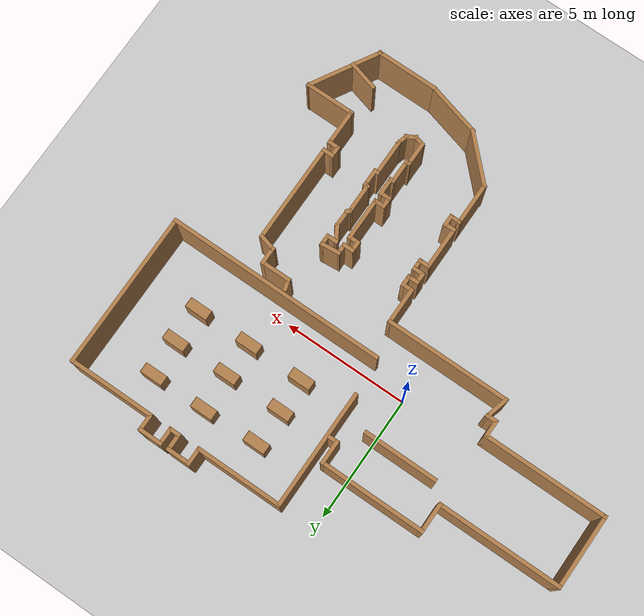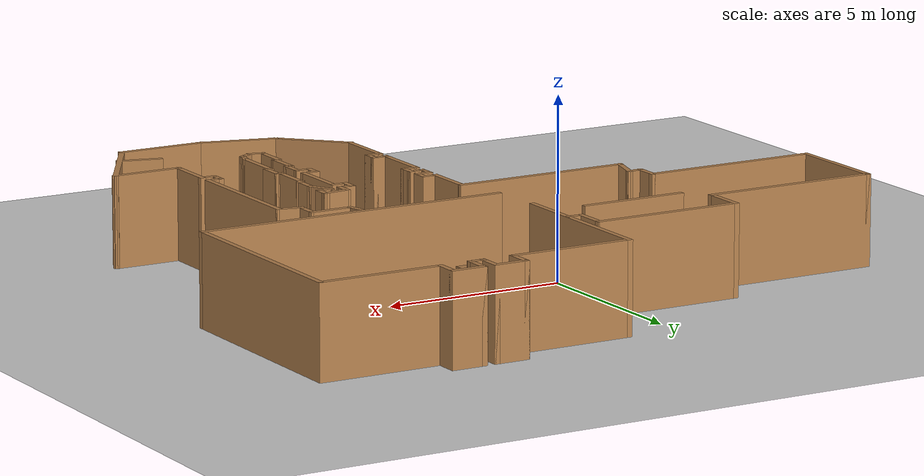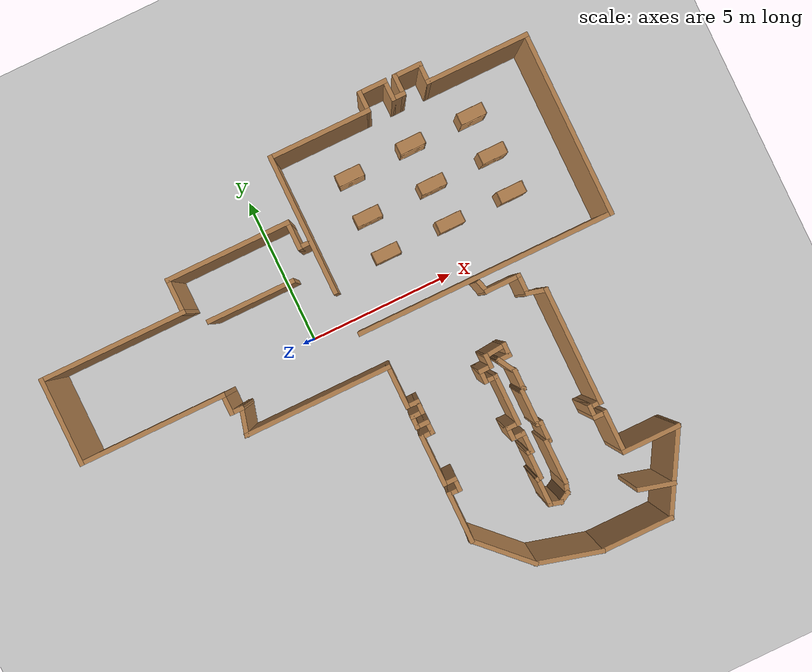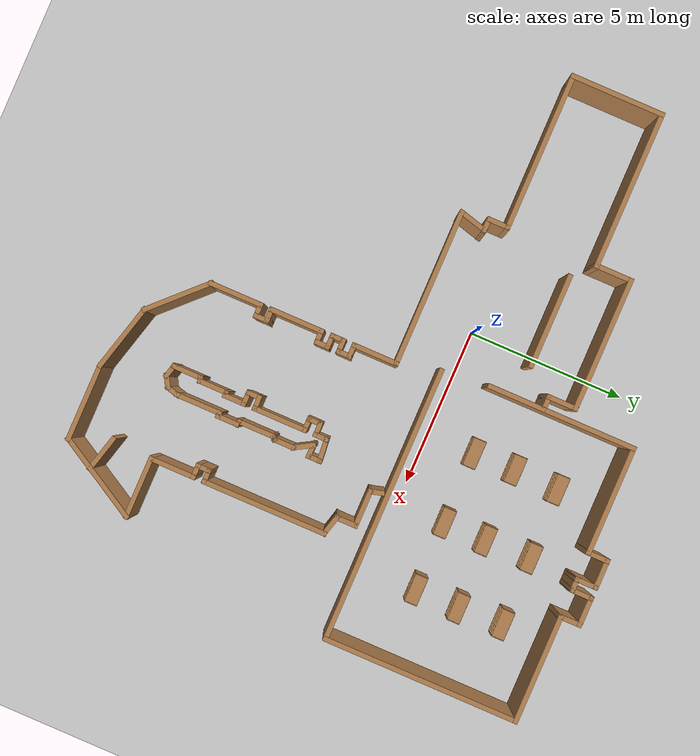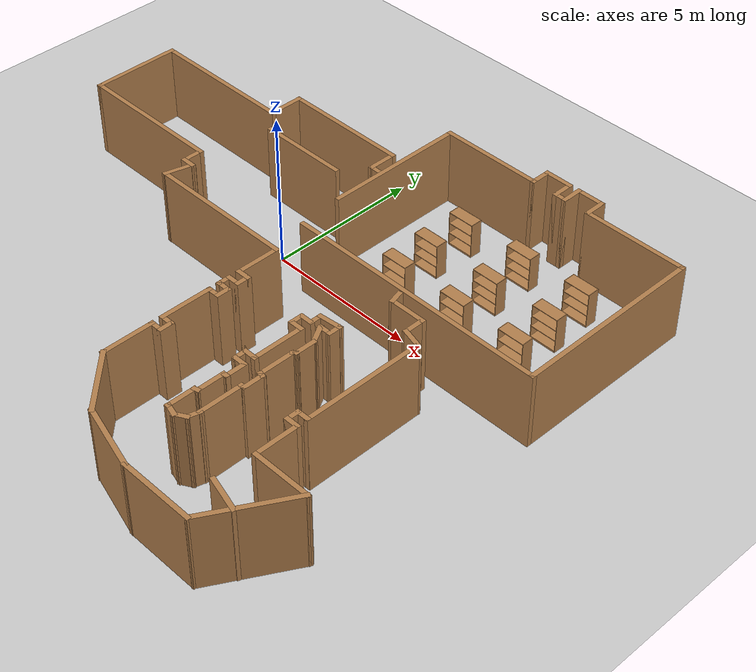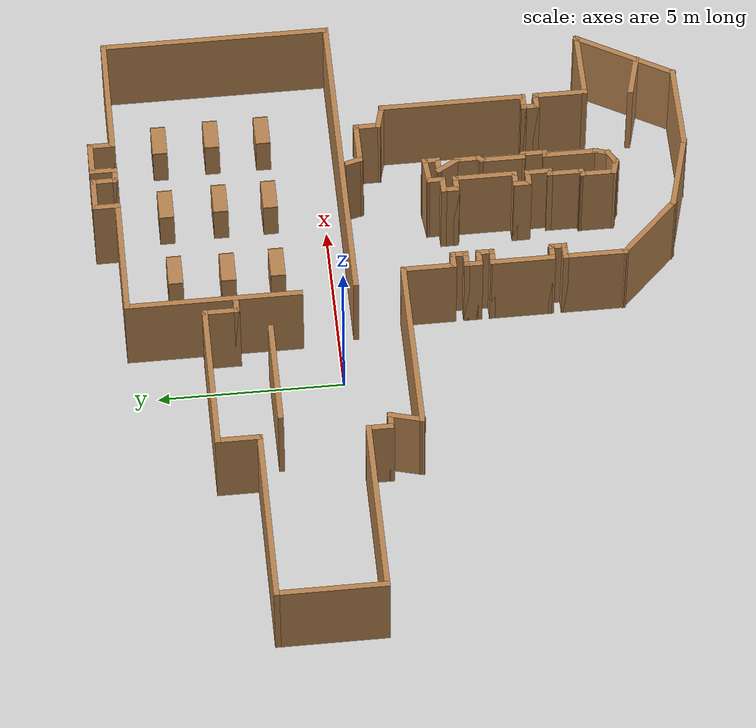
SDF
<sdf version="1.6">
 <world name="default">
  <light name="sun" type="directional">
   <pose>0 0 10 0 -0 0</pose>
   <diffuse>0.8 0.8 0.8 1</diffuse>
   <specular>0.1 0.1 0.1 1</specular>
   <attenuation>
    <range>1000</range>
    <constant>0.9</constant>
    <linear>0.01</linear>
    <quadratic>0.001</quadratic>
   </attenuation>
   <direction>-0.5 0.5 -1</direction>
  </light>
  <model name="ground_plane">
   <static>1</static>
   <link name="link">
    <collision name="collision">
     <geometry><plane><normal>0 0 1</normal><size>100 100</size></plane></geometry>
     <surface><friction><ode><mu>100</mu><mu2>50</mu2></ode></friction></surface>
    </collision>
    <visual name="visual">
     <cast_shadows>0</cast_shadows>
     <geometry><plane><normal>0 0 1</normal><size>100 100</size></plane></geometry>
     <material>
      <script><uri>file://media/materials/scripts/gazebo.material</uri><name>Gazebo/Grey</name></script>
     </material>
    </visual>
   </link>
  </model>
  <gravity>0 0 -9.8</gravity>
  <magnetic_field>6e-06 2.3e-05 -4.2e-05</magnetic_field>
  <atmosphere type="adiabatic"/>
  <physics name="default_physics" default="0" type="ode">
   <max_step_size>0.001</max_step_size>
   <real_time_factor>1</real_time_factor>
   <real_time_update_rate>1000</real_time_update_rate>
  </physics>
  <scene><ambient>0.4 0.4 0.4 1</ambient><background>0.7 0.7 0.7 1</background><shadows>1</shadows></scene>
  <spherical_coordinates>
   <surface_model>EARTH_WGS84</surface_model>
   <latitude_deg>0</latitude_deg>
   <longitude_deg>0</longitude_deg>
   <elevation>0</elevation>
   <heading_deg>0</heading_deg>
  </spherical_coordinates>
  <model name="Robita1_1">
   <pose>1.06807 -1.7719 0 0 -0 0</pose>
   <link name="Wall_104">
    <collision name="Wall_104_Collision">
     <geometry><box><size>0.5 0.15 2.5</size></box></geometry>
     <pose>0 0 1.25 0 -0 0</pose>
    </collision>
    <visual name="Wall_104_Visual">
     <pose>0 0 1.25 0 -0 0</pose>
     <geometry><box><size>0.5 0.15 2.5</size></box></geometry>
     <material>
      <script><uri>file://media/materials/scripts/gazebo.material</uri><name>Gazebo/Wood</name></script>
      <ambient>1 1 1 1</ambient>
     </material>
    </visual>
    <pose>3.64941 -1.1749 0 0 0 -1.5708</pose>
   </link>
   <link name="Wall_105">
    <collision name="Wall_105_Collision">
     <geometry><box><size>0.5 0.15 2.5</size></box></geometry>
     <pose>0 0 1.25 0 -0 0</pose>
    </collision>
    <visual name="Wall_105_Visual">
     <pose>0 0 1.25 0 -0 0</pose>
     <geometry><box><size>0.5 0.15 2.5</size></box></geometry>
     <material>
      <script><uri>file://media/materials/scripts/gazebo.material</uri><name>Gazebo/Wood</name></script>
      <ambient>1 1 1 1</ambient>
     </material>
    </visual>
    <pose>3.47441 -1.3499 0 0 -0 3.14159</pose>
   </link>
   <link name="Wall_106">
    <collision name="Wall_106_Collision">
     <geometry><box><size>0.5 0.15 2.5</size></box></geometry>
     <pose>0 0 1.25 0 -0 0</pose>
    </collision>
    <visual name="Wall_106_Visual">
     <pose>0 0 1.25 0 -0 0</pose>
     <geometry><box><size>0.5 0.15 2.5</size></box></geometry>
     <material>
      <script><uri>file://media/materials/scripts/gazebo.material</uri><name>Gazebo/Wood</name></script>
      <ambient>1 1 1 1</ambient>
     </material>
    </visual>
    <pose>3.29941 -1.5249 0 0 0 -1.5708</pose>
   </link>
   <link name="Wall_107">
    <collision name="Wall_107_Collision">
     <geometry><box><size>0.5 0.15 2.5</size></box></geometry>
     <pose>0 0 1.25 0 -0 0</pose>
    </collision>
    <visual name="Wall_107_Visual">
     <pose>0 0 1.25 0 -0 0</pose>
     <geometry><box><size>0.5 0.15 2.5</size></box></geometry>
     <material>
      <script><uri>file://media/materials/scripts/gazebo.material</uri><name>Gazebo/Wood</name></script>
      <ambient>1 1 1 1</ambient>
     </material>
    </visual>
    <pose>3.47441 -1.6999 0 0 -0 0</pose>
   </link>
   <link name="Wall_108">
    <collision name="Wall_108_Collision">
     <geometry><box><size>1.75 0.15 2.5</size></box></geometry>
     <pose>0 0 1.25 0 -0 0</pose>
    </collision>
    <visual name="Wall_108_Visual">
     <pose>0 0 1.25 0 -0 0</pose>
     <geometry><box><size>1.75 0.15 2.5</size></box></geometry>
     <material>
      <script><uri>file://media/materials/scripts/gazebo.material</uri><name>Gazebo/Wood</name></script>
      <ambient>1 1 1 1</ambient>
     </material>
    </visual>
    <pose>3.64941 -2.4999 0 0 0 -1.5708</pose>
   </link>
   <link name="Wall_112">
    <collision name="Wall_112_Collision">
     <geometry><box><size>0.5 0.15 2.5</size></box></geometry>
     <pose>0 0 1.25 0 -0 0</pose>
    </collision>
    <visual name="Wall_112_Visual">
     <pose>0 0 1.25 0 -0 0</pose>
     <geometry><box><size>0.5 0.15 2.5</size></box></geometry>
     <material>
      <script><uri>file://media/materials/scripts/gazebo.material</uri><name>Gazebo/Wood</name></script>
      <ambient>1 1 1 1</ambient>
     </material>
    </visual>
    <pose>3.47441 -3.2999 0 0 -0 3.14159</pose>
   </link>
   <link name="Wall_113">
    <collision name="Wall_113_Collision">
     <geometry><box><size>0.5 0.15 2.5</size></box></geometry>
     <pose>0 0 1.25 0 -0 0</pose>
    </collision>
    <visual name="Wall_113_Visual">
     <pose>0 0 1.25 0 -0 0</pose>
     <geometry><box><size>0.5 0.15 2.5</size></box></geometry>
     <material>
      <script><uri>file://media/materials/scripts/gazebo.material</uri><name>Gazebo/Wood</name></script>
      <ambient>1 1 1 1</ambient>
     </material>
    </visual>
    <pose>3.29941 -3.4749 0 0 0 -1.5708</pose>
   </link>
   <link name="Wall_114">
    <collision name="Wall_114_Collision">
     <geometry><box><size>0.5 0.15 2.5</size></box></geometry>
     <pose>0 0 1.25 0 -0 0</pose>
    </collision>
    <visual name="Wall_114_Visual">
     <pose>0 0 1.25 0 -0 0</pose>
     <geometry><box><size>0.5 0.15 2.5</size></box></geometry>
     <material>
      <script><uri>file://media/materials/scripts/gazebo.material</uri><name>Gazebo/Wood</name></script>
      <ambient>1 1 1 1</ambient>
     </material>
    </visual>
    <pose>3.47441 -3.6499 0 0 -0 0</pose>
   </link>
   <link name="Wall_115">
    <collision name="Wall_115_Collision">
     <geometry><box><size>0.75 0.15 2.5</size></box></geometry>
     <pose>0 0 1.25 0 -0 0</pose>
    </collision>
    <visual name="Wall_115_Visual">
     <pose>0 0 1.25 0 -0 0</pose>
     <geometry><box><size>0.75 0.15 2.5</size></box></geometry>
     <material>
      <script><uri>file://media/materials/scripts/gazebo.material</uri><name>Gazebo/Wood</name></script>
      <ambient>1 1 1 1</ambient>
     </material>
    </visual>
    <pose>3.64941 -3.9499 0 0 0 -1.5708</pose>
   </link>
   <link name="Wall_116">
    <collision name="Wall_116_Collision">
     <geometry><box><size>0.25 0.15 2.5</size></box></geometry>
     <pose>0 0 1.25 0 -0 0</pose>
    </collision>
    <visual name="Wall_116_Visual">
     <pose>0 0 1.25 0 -0 0</pose>
     <geometry><box><size>0.25 0.15 2.5</size></box></geometry>
     <material>
      <script><uri>file://media/materials/scripts/gazebo.material</uri><name>Gazebo/Wood</name></script>
      <ambient>1 1 1 1</ambient>
     </material>
    </visual>
    <pose>3.59941 -4.2499 0 0 -0 3.14159</pose>
   </link>
   <link name="Wall_117">
    <collision name="Wall_117_Collision">
     <geometry><box><size>1 0.15 2.5</size></box></geometry>
     <pose>0 0 1.25 0 -0 0</pose>
    </collision>
    <visual name="Wall_117_Visual">
     <pose>0 0 1.25 0 -0 0</pose>
     <geometry><box><size>1 0.15 2.5</size></box></geometry>
     <material>
      <script><uri>file://media/materials/scripts/gazebo.material</uri><name>Gazebo/Wood</name></script>
      <ambient>1 1 1 1</ambient>
     </material>
    </visual>
    <pose>3.54941 -4.6749 0 0 0 -1.5708</pose>
   </link>
   <link name="Wall_118">
    <collision name="Wall_118_Collision">
     <geometry><box><size>0.25 0.15 2.5</size></box></geometry>
     <pose>0 0 1.25 0 -0 0</pose>
    </collision>
    <visual name="Wall_118_Visual">
     <pose>0 0 1.25 0 -0 0</pose>
     <geometry><box><size>0.25 0.15 2.5</size></box></geometry>
     <material>
      <script><uri>file://media/materials/scripts/gazebo.material</uri><name>Gazebo/Wood</name></script>
      <ambient>1 1 1 1</ambient>
     </material>
    </visual>
    <pose>3.50111 -5.11284 0 0 0 -2.87979</pose>
   </link>
   <link name="Wall_119">
    <collision name="Wall_119_Collision">
     <geometry><box><size>1 0.15 2.5</size></box></geometry>
     <pose>0 0 1.25 0 -0 0</pose>
    </collision>
    <visual name="Wall_119_Visual">
     <pose>0 0 1.25 0 -0 0</pose>
     <geometry><box><size>1 0.15 2.5</size></box></geometry>
     <material>
      <script><uri>file://media/materials/scripts/gazebo.material</uri><name>Gazebo/Wood</name></script>
      <ambient>1 1 1 1</ambient>
     </material>
    </visual>
    <pose>3.45282 -5.55078 0 0 0 -1.5708</pose>
   </link>
   <link name="Wall_121">
    <collision name="Wall_121_Collision">
     <geometry><box><size>0.5 0.15 2.5</size></box></geometry>
     <pose>0 0 1.25 0 -0 0</pose>
    </collision>
    <visual name="Wall_121_Visual">
     <pose>0 0 1.25 0 -0 0</pose>
     <geometry><box><size>0.5 0.15 2.5</size></box></geometry>
     <material>
      <script><uri>file://media/materials/scripts/gazebo.material</uri><name>Gazebo/Wood</name></script>
      <ambient>1 1 1 1</ambient>
     </material>
    </visual>
    <pose>3.62186 -6.02107 0 0 0 -0.261799</pose>
   </link>
   <link name="Wall_122">
    <collision name="Wall_122_Collision">
     <geometry><box><size>0.5 0.15 2.5</size></box></geometry>
     <pose>0 0 1.25 0 -0 0</pose>
    </collision>
    <visual name="Wall_122_Visual">
     <pose>0 0 1.25 0 -0 0</pose>
     <geometry><box><size>0.5 0.15 2.5</size></box></geometry>
     <material>
      <script><uri>file://media/materials/scripts/gazebo.material</uri><name>Gazebo/Wood</name></script>
      <ambient>1 1 1 1</ambient>
     </material>
    </visual>
    <pose>3.94245 -5.97887 0 0 -0 0.523599</pose>
   </link>
   <link name="Wall_123">
    <collision name="Wall_123_Collision">
     <geometry><box><size>0.5 0.15 2.5</size></box></geometry>
     <pose>0 0 1.25 0 -0 0</pose>
    </collision>
    <visual name="Wall_123_Visual">
     <pose>0 0 1.25 0 -0 0</pose>
     <geometry><box><size>0.5 0.15 2.5</size></box></geometry>
     <material>
      <script><uri>file://media/materials/scripts/gazebo.material</uri><name>Gazebo/Wood</name></script>
      <ambient>1 1 1 1</ambient>
     </material>
    </visual>
    <pose>4.13929 -5.72233 0 0 -0 1.309</pose>
   </link>
   <link name="Wall_126">
    <collision name="Wall_126_Collision">
     <geometry><box><size>1.5 0.15 2.5</size></box></geometry>
     <pose>0 0 1.25 0 -0 0</pose>
    </collision>
    <visual name="Wall_126_Visual">
     <pose>0 0 1.25 0 -0 0</pose>
     <geometry><box><size>1.5 0.15 2.5</size></box></geometry>
     <material>
      <script><uri>file://media/materials/scripts/gazebo.material</uri><name>Gazebo/Wood</name></script>
      <ambient>1 1 1 1</ambient>
     </material>
    </visual>
    <pose>4.18459 -4.87829 0 0 -0 1.5708</pose>
   </link>
   <link name="Wall_127">
    <collision name="Wall_127_Collision">
     <geometry><box><size>0.25 0.15 2.5</size></box></geometry>
     <pose>0 0 1.25 0 -0 0</pose>
    </collision>
    <visual name="Wall_127_Visual">
     <pose>0 0 1.25 0 -0 0</pose>
     <geometry><box><size>0.25 0.15 2.5</size></box></geometry>
     <material>
      <script><uri>file://media/materials/scripts/gazebo.material</uri><name>Gazebo/Wood</name></script>
      <ambient>1 1 1 1</ambient>
     </material>
    </visual>
    <pose>4.23459 -4.20329 0 0 -0 0</pose>
   </link>
   <link name="Wall_128">
    <collision name="Wall_128_Collision">
     <geometry><box><size>0.75 0.15 2.5</size></box></geometry>
     <pose>0 0 1.25 0 -0 0</pose>
    </collision>
    <visual name="Wall_128_Visual">
     <pose>0 0 1.25 0 -0 0</pose>
     <geometry><box><size>0.75 0.15 2.5</size></box></geometry>
     <material>
      <script><uri>file://media/materials/scripts/gazebo.material</uri><name>Gazebo/Wood</name></script>
      <ambient>1 1 1 1</ambient>
     </material>
    </visual>
    <pose>4.28459 -3.90329 0 0 -0 1.5708</pose>
   </link>
   <link name="Wall_129">
    <collision name="Wall_129_Collision">
     <geometry><box><size>0.25 0.15 2.5</size></box></geometry>
     <pose>0 0 1.25 0 -0 0</pose>
    </collision>
    <visual name="Wall_129_Visual">
     <pose>0 0 1.25 0 -0 0</pose>
     <geometry><box><size>0.25 0.15 2.5</size></box></geometry>
     <material>
      <script><uri>file://media/materials/scripts/gazebo.material</uri><name>Gazebo/Wood</name></script>
      <ambient>1 1 1 1</ambient>
     </material>
    </visual>
    <pose>4.23629 -3.59035 0 0 -0 2.87979</pose>
   </link>
   <link name="Wall_130">
    <collision name="Wall_130_Collision">
     <geometry><box><size>1.25 0.15 2.5</size></box></geometry>
     <pose>0 0 1.25 0 -0 0</pose>
    </collision>
    <visual name="Wall_130_Visual">
     <pose>0 0 1.25 0 -0 0</pose>
     <geometry><box><size>1.25 0.15 2.5</size></box></geometry>
     <material>
      <script><uri>file://media/materials/scripts/gazebo.material</uri><name>Gazebo/Wood</name></script>
      <ambient>1 1 1 1</ambient>
     </material>
    </visual>
    <pose>4.18799 -3.02741 0 0 -0 1.5708</pose>
   </link>
   <link name="Wall_131">
    <collision name="Wall_131_Collision">
     <geometry><box><size>0.25 0.15 2.5</size></box></geometry>
     <pose>0 0 1.25 0 -0 0</pose>
    </collision>
    <visual name="Wall_131_Visual">
     <pose>0 0 1.25 0 -0 0</pose>
     <geometry><box><size>0.25 0.15 2.5</size></box></geometry>
     <material>
      <script><uri>file://media/materials/scripts/gazebo.material</uri><name>Gazebo/Wood</name></script>
      <ambient>1 1 1 1</ambient>
     </material>
    </visual>
    <pose>4.22335 -2.44205 0 0 -0 0.785398</pose>
   </link>
   <link name="Wall_132">
    <collision name="Wall_132_Collision">
     <geometry><box><size>0.75 0.15 2.5</size></box></geometry>
     <pose>0 0 1.25 0 -0 0</pose>
    </collision>
    <visual name="Wall_132_Visual">
     <pose>0 0 1.25 0 -0 0</pose>
     <geometry><box><size>0.75 0.15 2.5</size></box></geometry>
     <material>
      <script><uri>file://media/materials/scripts/gazebo.material</uri><name>Gazebo/Wood</name></script>
      <ambient>1 1 1 1</ambient>
     </material>
    </visual>
    <pose>4.2587 -2.1067 0 0 -0 1.5708</pose>
   </link>
   <link name="Wall_135">
    <collision name="Wall_135_Collision">
     <geometry><box><size>0.75 0.15 2.5</size></box></geometry>
     <pose>0 0 1.25 0 -0 0</pose>
    </collision>
    <visual name="Wall_135_Visual">
     <pose>0 0 1.25 0 -0 0</pose>
     <geometry><box><size>0.75 0.15 2.5</size></box></geometry>
     <material>
      <script><uri>file://media/materials/scripts/gazebo.material</uri><name>Gazebo/Wood</name></script>
      <ambient>1 1 1 1</ambient>
     </material>
    </visual>
    <pose>4.1087 -1.54689 0 0 -0 2.0944</pose>
   </link>
   <link name="Wall_136">
    <collision name="Wall_136_Collision">
     <geometry><box><size>0.5 0.15 2.5</size></box></geometry>
     <pose>0 0 1.25 0 -0 0</pose>
    </collision>
    <visual name="Wall_136_Visual">
     <pose>0 0 1.25 0 -0 0</pose>
     <geometry><box><size>0.5 0.15 2.5</size></box></geometry>
     <material>
      <script><uri>file://media/materials/scripts/gazebo.material</uri><name>Gazebo/Wood</name></script>
      <ambient>1 1 1 1</ambient>
     </material>
    </visual>
    <pose>4.13393 -1.28713 0 0 0 -0.000242</pose>
   </link>
   <link name="Wall_137">
    <collision name="Wall_137_Collision">
     <geometry><box><size>0.5 0.15 2.5</size></box></geometry>
     <pose>0 0 1.25 0 -0 0</pose>
    </collision>
    <visual name="Wall_137_Visual">
     <pose>0 0 1.25 0 -0 0</pose>
     <geometry><box><size>0.5 0.15 2.5</size></box></geometry>
     <material>
      <script><uri>file://media/materials/scripts/gazebo.material</uri><name>Gazebo/Wood</name></script>
      <ambient>1 1 1 1</ambient>
     </material>
    </visual>
    <pose>4.30916 -1.11217 0 0 -0 1.5708</pose>
   </link>
   <link name="Wall_138">
    <collision name="Wall_138_Collision">
     <geometry><box><size>0.812281 0.15 2.5</size></box></geometry>
     <pose>0 0 1.25 0 -0 0</pose>
    </collision>
    <visual name="Wall_138_Visual">
     <pose>0 0 1.25 0 -0 0</pose>
     <geometry><box><size>0.812281 0.15 2.5</size></box></geometry>
     <material>
      <script><uri>file://media/materials/scripts/gazebo.material</uri><name>Gazebo/Wood</name></script>
      <ambient>1 1 1 1</ambient>
     </material>
    </visual>
    <pose>3.97928 -0.968534 0 0 0 -3.0468</pose>
   </link>
   <link name="Wall_140">
    <collision name="Wall_140_Collision">
     <geometry><box><size>1.25 0.15 2.5</size></box></geometry>
     <pose>0 0 1.25 0 -0 0</pose>
    </collision>
    <visual name="Wall_140_Visual">
     <pose>0 0 1.25 0 -0 0</pose>
     <geometry><box><size>1.25 0.15 2.5</size></box></geometry>
     <material>
      <script><uri>file://media/materials/scripts/gazebo.material</uri><name>Gazebo/Wood</name></script>
      <ambient>1 1 1 1</ambient>
     </material>
    </visual>
    <pose>6.66221 -6.90662 0 0 0 -0.261799</pose>
   </link>
   <link name="Wall_16">
    <collision name="Wall_16_Collision">
     <geometry><box><size>0.75 0.15 2.5</size></box></geometry>
     <pose>0 0 1.25 0 -0 0</pose>
    </collision>
    <visual name="Wall_16_Visual">
     <pose>0 0 1.25 0 -0 0</pose>
     <geometry><box><size>0.75 0.15 2.5</size></box></geometry>
     <material>
      <script><uri>file://media/materials/scripts/gazebo.material</uri><name>Gazebo/Wood</name></script>
      <ambient>1 1 1 1</ambient>
     </material>
    </visual>
    <pose>-4.20078 1.12035 0 0 0 -1.5708</pose>
   </link>
   <link name="Wall_17">
    <collision name="Wall_17_Collision">
     <geometry><box><size>0.5 0.15 2.5</size></box></geometry>
     <pose>0 0 1.25 0 -0 0</pose>
    </collision>
    <visual name="Wall_17_Visual">
     <pose>0 0 1.25 0 -0 0</pose>
     <geometry><box><size>0.5 0.15 2.5</size></box></geometry>
     <material>
      <script><uri>file://media/materials/scripts/gazebo.material</uri><name>Gazebo/Wood</name></script>
      <ambient>1 1 1 1</ambient>
     </material>
    </visual>
    <pose>-4.02578 0.820348 0 0 -0 0</pose>
   </link>
   <link name="Wall_18">
    <collision name="Wall_18_Collision">
     <geometry><box><size>1 0.15 2.5</size></box></geometry>
     <pose>0 0 1.25 0 -0 0</pose>
    </collision>
    <visual name="Wall_18_Visual">
     <pose>0 0 1.25 0 -0 0</pose>
     <geometry><box><size>1 0.15 2.5</size></box></geometry>
     <material>
      <script><uri>file://media/materials/scripts/gazebo.material</uri><name>Gazebo/Wood</name></script>
      <ambient>1 1 1 1</ambient>
     </material>
    </visual>
    <pose>-3.96077 0.409829 0 0 0 -1.8326</pose>
   </link>
   <link name="Wall_19">
    <collision name="Wall_19_Collision">
     <geometry><box><size>5 0.15 2.5</size></box></geometry>
     <pose>0 0 1.25 0 -0 0</pose>
    </collision>
    <visual name="Wall_19_Visual">
     <pose>0 0 1.25 0 -0 0</pose>
     <geometry><box><size>5 0.15 2.5</size></box></geometry>
     <material>
      <script><uri>file://media/materials/scripts/gazebo.material</uri><name>Gazebo/Wood</name></script>
      <ambient>1 1 1 1</ambient>
     </material>
    </visual>
    <pose>-1.64577 -0.000689 0 0 -0 0</pose>
   </link>
   <link name="Wall_20">
    <collision name="Wall_20_Collision">
     <geometry><box><size>1.5 0.15 2.5</size></box></geometry>
     <pose>0 0 1.25 0 -0 0</pose>
    </collision>
    <visual name="Wall_20_Visual">
     <pose>0 0 1.25 0 -0 0</pose>
     <geometry><box><size>1.5 0.15 2.5</size></box></geometry>
     <material>
      <script><uri>file://media/materials/scripts/gazebo.material</uri><name>Gazebo/Wood</name></script>
      <ambient>1 1 1 1</ambient>
     </material>
    </visual>
    <pose>0.779229 -0.675689 0 0 0 -1.5708</pose>
   </link>
   <link name="Wall_21">
    <collision name="Wall_21_Collision">
     <geometry><box><size>0.5 0.15 2.5</size></box></geometry>
     <pose>0 0 1.25 0 -0 0</pose>
    </collision>
    <visual name="Wall_21_Visual">
     <pose>0 0 1.25 0 -0 0</pose>
     <geometry><box><size>0.5 0.15 2.5</size></box></geometry>
     <material>
      <script><uri>file://media/materials/scripts/gazebo.material</uri><name>Gazebo/Wood</name></script>
      <ambient>1 1 1 1</ambient>
     </material>
    </visual>
    <pose>0.954229 -1.35069 0 0 -0 0</pose>
   </link>
   <link name="Wall_22">
    <collision name="Wall_22_Collision">
     <geometry><box><size>0.5 0.15 2.5</size></box></geometry>
     <pose>0 0 1.25 0 -0 0</pose>
    </collision>
    <visual name="Wall_22_Visual">
     <pose>0 0 1.25 0 -0 0</pose>
     <geometry><box><size>0.5 0.15 2.5</size></box></geometry>
     <material>
      <script><uri>file://media/materials/scripts/gazebo.material</uri><name>Gazebo/Wood</name></script>
      <ambient>1 1 1 1</ambient>
     </material>
    </visual>
    <pose>1.12923 -1.52569 0 0 0 -1.5708</pose>
   </link>
   <link name="Wall_25">
    <collision name="Wall_25_Collision">
     <geometry><box><size>0.5 0.15 2.5</size></box></geometry>
     <pose>0 0 1.25 0 -0 0</pose>
    </collision>
    <visual name="Wall_25_Visual">
     <pose>0 0 1.25 0 -0 0</pose>
     <geometry><box><size>0.5 0.15 2.5</size></box></geometry>
     <material>
      <script><uri>file://media/materials/scripts/gazebo.material</uri><name>Gazebo/Wood</name></script>
      <ambient>1 1 1 1</ambient>
     </material>
    </visual>
    <pose>0.954229 -1.70069 0 0 -0 3.14159</pose>
   </link>
   <link name="Wall_26">
    <collision name="Wall_26_Collision">
     <geometry><box><size>0.5 0.15 2.5</size></box></geometry>
     <pose>0 0 1.25 0 -0 0</pose>
    </collision>
    <visual name="Wall_26_Visual">
     <pose>0 0 1.25 0 -0 0</pose>
     <geometry><box><size>0.5 0.15 2.5</size></box></geometry>
     <material>
      <script><uri>file://media/materials/scripts/gazebo.material</uri><name>Gazebo/Wood</name></script>
      <ambient>1 1 1 1</ambient>
     </material>
    </visual>
    <pose>0.779229 -1.87569 0 0 0 -1.5708</pose>
   </link>
   <link name="Wall_27">
    <collision name="Wall_27_Collision">
     <geometry><box><size>0.5 0.15 2.5</size></box></geometry>
     <pose>0 0 1.25 0 -0 0</pose>
    </collision>
    <visual name="Wall_27_Visual">
     <pose>0 0 1.25 0 -0 0</pose>
     <geometry><box><size>0.5 0.15 2.5</size></box></geometry>
     <material>
      <script><uri>file://media/materials/scripts/gazebo.material</uri><name>Gazebo/Wood</name></script>
      <ambient>1 1 1 1</ambient>
     </material>
    </visual>
    <pose>0.954229 -2.05069 0 0 -0 0</pose>
   </link>
   <link name="Wall_28">
    <collision name="Wall_28_Collision">
     <geometry><box><size>0.5 0.15 2.5</size></box></geometry>
     <pose>0 0 1.25 0 -0 0</pose>
    </collision>
    <visual name="Wall_28_Visual">
     <pose>0 0 1.25 0 -0 0</pose>
     <geometry><box><size>0.5 0.15 2.5</size></box></geometry>
     <material>
      <script><uri>file://media/materials/scripts/gazebo.material</uri><name>Gazebo/Wood</name></script>
      <ambient>1 1 1 1</ambient>
     </material>
    </visual>
    <pose>1.12923 -2.22569 0 0 0 -1.5708</pose>
   </link>
   <link name="Wall_29">
    <collision name="Wall_29_Collision">
     <geometry><box><size>0.5 0.15 2.5</size></box></geometry>
     <pose>0 0 1.25 0 -0 0</pose>
    </collision>
    <visual name="Wall_29_Visual">
     <pose>0 0 1.25 0 -0 0</pose>
     <geometry><box><size>0.5 0.15 2.5</size></box></geometry>
     <material>
      <script><uri>file://media/materials/scripts/gazebo.material</uri><name>Gazebo/Wood</name></script>
      <ambient>1 1 1 1</ambient>
     </material>
    </visual>
    <pose>0.954229 -2.40069 0 0 -0 3.14159</pose>
   </link>
   <link name="Wall_3">
    <collision name="Wall_3_Collision">
     <geometry><box><size>3 0.15 2.5</size></box></geometry>
     <pose>0 0 1.25 0 -0 0</pose>
    </collision>
    <visual name="Wall_3_Visual">
     <pose>0 0 1.25 0 -0 0</pose>
     <geometry><box><size>3 0.15 2.5</size></box></geometry>
     <material>
      <script><uri>file://media/materials/scripts/gazebo.material</uri><name>Gazebo/Wood</name></script>
      <ambient>1 1 1 1</ambient>
     </material>
    </visual>
    <pose>-9.05077 2.84535 0 0 0 -1.5708</pose>
   </link>
   <link name="Wall_31">
    <collision name="Wall_31_Collision">
     <geometry><box><size>1.75 0.15 2.5</size></box></geometry>
     <pose>0 0 1.25 0 -0 0</pose>
    </collision>
    <visual name="Wall_31_Visual">
     <pose>0 0 1.25 0 -0 0</pose>
     <geometry><box><size>1.75 0.15 2.5</size></box></geometry>
     <material>
      <script><uri>file://media/materials/scripts/gazebo.material</uri><name>Gazebo/Wood</name></script>
      <ambient>1 1 1 1</ambient>
     </material>
    </visual>
    <pose>0.779229 -3.20069 0 0 0 -1.5708</pose>
   </link>
   <link name="Wall_32">
    <collision name="Wall_32_Collision">
     <geometry><box><size>0.5 0.15 2.5</size></box></geometry>
     <pose>0 0 1.25 0 -0 0</pose>
    </collision>
    <visual name="Wall_32_Visual">
     <pose>0 0 1.25 0 -0 0</pose>
     <geometry><box><size>0.5 0.15 2.5</size></box></geometry>
     <material>
      <script><uri>file://media/materials/scripts/gazebo.material</uri><name>Gazebo/Wood</name></script>
      <ambient>1 1 1 1</ambient>
     </material>
    </visual>
    <pose>0.954229 -4.00069 0 0 -0 0</pose>
   </link>
   <link name="Wall_35">
    <collision name="Wall_35_Collision">
     <geometry><box><size>0.5 0.15 2.5</size></box></geometry>
     <pose>0 0 1.25 0 -0 0</pose>
    </collision>
    <visual name="Wall_35_Visual">
     <pose>0 0 1.25 0 -0 0</pose>
     <geometry><box><size>0.5 0.15 2.5</size></box></geometry>
     <material>
      <script><uri>file://media/materials/scripts/gazebo.material</uri><name>Gazebo/Wood</name></script>
      <ambient>1 1 1 1</ambient>
     </material>
    </visual>
    <pose>1.12923 -4.17569 0 0 0 -1.5708</pose>
   </link>
   <link name="Wall_38">
    <collision name="Wall_38_Collision">
     <geometry><box><size>0.5 0.15 2.5</size></box></geometry>
     <pose>0 0 1.25 0 -0 0</pose>
    </collision>
    <visual name="Wall_38_Visual">
     <pose>0 0 1.25 0 -0 0</pose>
     <geometry><box><size>0.5 0.15 2.5</size></box></geometry>
     <material>
      <script><uri>file://media/materials/scripts/gazebo.material</uri><name>Gazebo/Wood</name></script>
      <ambient>1 1 1 1</ambient>
     </material>
    </visual>
    <pose>0.954229 -4.35069 0 0 -0 3.14159</pose>
   </link>
   <link name="Wall_39">
    <collision name="Wall_39_Collision">
     <geometry><box><size>1.75 0.15 2.5</size></box></geometry>
     <pose>0 0 1.25 0 -0 0</pose>
    </collision>
    <visual name="Wall_39_Visual">
     <pose>0 0 1.25 0 -0 0</pose>
     <geometry><box><size>1.75 0.15 2.5</size></box></geometry>
     <material>
      <script><uri>file://media/materials/scripts/gazebo.material</uri><name>Gazebo/Wood</name></script>
      <ambient>1 1 1 1</ambient>
     </material>
    </visual>
    <pose>0.779229 -5.15069 0 0 0 -1.5708</pose>
   </link>
   <link name="Wall_4">
    <collision name="Wall_4_Collision">
     <geometry><box><size>5 0.15 2.5</size></box></geometry>
     <pose>0 0 1.25 0 -0 0</pose>
    </collision>
    <visual name="Wall_4_Visual">
     <pose>0 0 1.25 0 -0 0</pose>
     <geometry><box><size>5 0.15 2.5</size></box></geometry>
     <material>
      <script><uri>file://media/materials/scripts/gazebo.material</uri><name>Gazebo/Wood</name></script>
      <ambient>1 1 1 1</ambient>
     </material>
    </visual>
    <pose>-6.62577 1.42035 0 0 -0 0</pose>
   </link>
   <link name="Wall_41">
    <collision name="Wall_41_Collision">
     <geometry><box><size>2.25 0.15 2.5</size></box></geometry>
     <pose>0 0 1.25 0 -0 0</pose>
    </collision>
    <visual name="Wall_41_Visual">
     <pose>0 0 1.25 0 -0 0</pose>
     <geometry><box><size>2.25 0.15 2.5</size></box></geometry>
     <material>
      <script><uri>file://media/materials/scripts/gazebo.material</uri><name>Gazebo/Wood</name></script>
      <ambient>1 1 1 1</ambient>
     </material>
    </visual>
    <pose>1.52169 -6.69315 0 0 0 -0.785398</pose>
   </link>
   <link name="Wall_42">
    <collision name="Wall_42_Collision">
     <geometry><box><size>2.25 0.15 2.5</size></box></geometry>
     <pose>0 0 1.25 0 -0 0</pose>
    </collision>
    <visual name="Wall_42_Visual">
     <pose>0 0 1.25 0 -0 0</pose>
     <geometry><box><size>2.25 0.15 2.5</size></box></geometry>
     <material>
      <script><uri>file://media/materials/scripts/gazebo.material</uri><name>Gazebo/Wood</name></script>
      <ambient>1 1 1 1</ambient>
     </material>
    </visual>
    <pose>3.27838 -7.70737 0 0 0 -0.261799</pose>
   </link>
   <link name="Wall_43">
    <collision name="Wall_43_Collision">
     <geometry><box><size>2.5 0.15 2.5</size></box></geometry>
     <pose>0 0 1.25 0 -0 0</pose>
    </collision>
    <visual name="Wall_43_Visual">
     <pose>0 0 1.25 0 -0 0</pose>
     <geometry><box><size>2.5 0.15 2.5</size></box></geometry>
     <material>
      <script><uri>file://media/materials/scripts/gazebo.material</uri><name>Gazebo/Wood</name></script>
      <ambient>1 1 1 1</ambient>
     </material>
    </visual>
    <pose>5.4676 -7.97913 0 0 -0 0</pose>
   </link>
   <link name="Wall_44">
    <collision name="Wall_44_Collision">
     <geometry><box><size>3 0.15 2.5</size></box></geometry>
     <pose>0 0 1.25 0 -0 0</pose>
    </collision>
    <visual name="Wall_44_Visual">
     <pose>0 0 1.25 0 -0 0</pose>
     <geometry><box><size>3 0.15 2.5</size></box></geometry>
     <material>
      <script><uri>file://media/materials/scripts/gazebo.material</uri><name>Gazebo/Wood</name></script>
      <ambient>1 1 1 1</ambient>
     </material>
    </visual>
    <pose>7.3551 -6.74505 0 0 -0 1.0472</pose>
   </link>
   <link name="Wall_47">
    <collision name="Wall_47_Collision">
     <geometry><box><size>2 0.15 2.5</size></box></geometry>
     <pose>0 0 1.25 0 -0 0</pose>
    </collision>
    <visual name="Wall_47_Visual">
     <pose>0 0 1.25 0 -0 0</pose>
     <geometry><box><size>2 0.15 2.5</size></box></geometry>
     <material>
      <script><uri>file://media/materials/scripts/gazebo.material</uri><name>Gazebo/Wood</name></script>
      <ambient>1 1 1 1</ambient>
     </material>
    </visual>
    <pose>7.1426 -5.51096 0 0 -0 3.14159</pose>
   </link>
   <link name="Wall_48">
    <collision name="Wall_48_Collision">
     <geometry><box><size>1.5 0.15 2.5</size></box></geometry>
     <pose>0 0 1.25 0 -0 0</pose>
    </collision>
    <visual name="Wall_48_Visual">
     <pose>0 0 1.25 0 -0 0</pose>
     <geometry><box><size>1.5 0.15 2.5</size></box></geometry>
     <material>
      <script><uri>file://media/materials/scripts/gazebo.material</uri><name>Gazebo/Wood</name></script>
      <ambient>1 1 1 1</ambient>
     </material>
    </visual>
    <pose>6.2176 -4.83596 0 0 -0 1.5708</pose>
   </link>
   <link name="Wall_49">
    <collision name="Wall_49_Collision">
     <geometry><box><size>0.5 0.15 2.5</size></box></geometry>
     <pose>0 0 1.25 0 -0 0</pose>
    </collision>
    <visual name="Wall_49_Visual">
     <pose>0 0 1.25 0 -0 0</pose>
     <geometry><box><size>0.5 0.15 2.5</size></box></geometry>
     <material>
      <script><uri>file://media/materials/scripts/gazebo.material</uri><name>Gazebo/Wood</name></script>
      <ambient>1 1 1 1</ambient>
     </material>
    </visual>
    <pose>6.0426 -4.16096 0 0 -0 3.14159</pose>
   </link>
   <link name="Wall_50">
    <collision name="Wall_50_Collision">
     <geometry><box><size>0.5 0.15 2.5</size></box></geometry>
     <pose>0 0 1.25 0 -0 0</pose>
    </collision>
    <visual name="Wall_50_Visual">
     <pose>0 0 1.25 0 -0 0</pose>
     <geometry><box><size>0.5 0.15 2.5</size></box></geometry>
     <material>
      <script><uri>file://media/materials/scripts/gazebo.material</uri><name>Gazebo/Wood</name></script>
      <ambient>1 1 1 1</ambient>
     </material>
    </visual>
    <pose>5.8676 -3.98596 0 0 -0 1.5708</pose>
   </link>
   <link name="Wall_51">
    <collision name="Wall_51_Collision">
     <geometry><box><size>0.5 0.15 2.5</size></box></geometry>
     <pose>0 0 1.25 0 -0 0</pose>
    </collision>
    <visual name="Wall_51_Visual">
     <pose>0 0 1.25 0 -0 0</pose>
     <geometry><box><size>0.5 0.15 2.5</size></box></geometry>
     <material>
      <script><uri>file://media/materials/scripts/gazebo.material</uri><name>Gazebo/Wood</name></script>
      <ambient>1 1 1 1</ambient>
     </material>
    </visual>
    <pose>6.0426 -3.81096 0 0 -0 0</pose>
   </link>
   <link name="Wall_52">
    <collision name="Wall_52_Collision">
     <geometry><box><size>4 0.15 2.5</size></box></geometry>
     <pose>0 0 1.25 0 -0 0</pose>
    </collision>
    <visual name="Wall_52_Visual">
     <pose>0 0 1.25 0 -0 0</pose>
     <geometry><box><size>4 0.15 2.5</size></box></geometry>
     <material>
      <script><uri>file://media/materials/scripts/gazebo.material</uri><name>Gazebo/Wood</name></script>
      <ambient>1 1 1 1</ambient>
     </material>
    </visual>
    <pose>6.2176 -1.88596 0 0 -0 1.5708</pose>
   </link>
   <link name="Wall_54">
    <collision name="Wall_54_Collision">
     <geometry><box><size>5 0.15 2.5</size></box></geometry>
     <pose>0 0 1.25 0 -0 0</pose>
    </collision>
    <visual name="Wall_54_Visual">
     <pose>0 0 1.25 0 -0 0</pose>
     <geometry><box><size>5 0.15 2.5</size></box></geometry>
     <material>
      <script><uri>file://media/materials/scripts/gazebo.material</uri><name>Gazebo/Wood</name></script>
      <ambient>1 1 1 1</ambient>
     </material>
    </visual>
    <pose>-6.62577 4.27035 0 0 -0 0</pose>
   </link>
   <link name="Wall_55">
    <collision name="Wall_55_Collision">
     <geometry><box><size>1.25 0.15 2.5</size></box></geometry>
     <pose>0 0 1.25 0 -0 0</pose>
    </collision>
    <visual name="Wall_55_Visual">
     <pose>0 0 1.25 0 -0 0</pose>
     <geometry><box><size>1.25 0.15 2.5</size></box></geometry>
     <material>
      <script><uri>file://media/materials/scripts/gazebo.material</uri><name>Gazebo/Wood</name></script>
      <ambient>1 1 1 1</ambient>
     </material>
    </visual>
    <pose>-4.20078 4.82035 0 0 -0 1.5708</pose>
   </link>
   <link name="Wall_56">
    <collision name="Wall_56_Collision">
     <geometry><box><size>4.25 0.15 2.5</size></box></geometry>
     <pose>0 0 1.25 0 -0 0</pose>
    </collision>
    <visual name="Wall_56_Visual">
     <pose>0 0 1.25 0 -0 0</pose>
     <geometry><box><size>4.25 0.15 2.5</size></box></geometry>
     <material>
      <script><uri>file://media/materials/scripts/gazebo.material</uri><name>Gazebo/Wood</name></script>
      <ambient>1 1 1 1</ambient>
     </material>
    </visual>
    <pose>-2.15077 5.37035 0 0 -0 0</pose>
   </link>
   <link name="Wall_57">
    <collision name="Wall_57_Collision">
     <geometry><box><size>1 0.15 2.5</size></box></geometry>
     <pose>0 0 1.25 0 -0 0</pose>
    </collision>
    <visual name="Wall_57_Visual">
     <pose>0 0 1.25 0 -0 0</pose>
     <geometry><box><size>1 0.15 2.5</size></box></geometry>
     <material>
      <script><uri>file://media/materials/scripts/gazebo.material</uri><name>Gazebo/Wood</name></script>
      <ambient>1 1 1 1</ambient>
     </material>
    </visual>
    <pose>-0.100775 4.94535 0 0 0 -1.5708</pose>
   </link>
   <link name="Wall_58">
    <collision name="Wall_58_Collision">
     <geometry><box><size>0.5 0.15 2.5</size></box></geometry>
     <pose>0 0 1.25 0 -0 0</pose>
    </collision>
    <visual name="Wall_58_Visual">
     <pose>0 0 1.25 0 -0 0</pose>
     <geometry><box><size>0.5 0.15 2.5</size></box></geometry>
     <material>
      <script><uri>file://media/materials/scripts/gazebo.material</uri><name>Gazebo/Wood</name></script>
      <ambient>1 1 1 1</ambient>
     </material>
    </visual>
    <pose>0.074225 4.52035 0 0 -0 0</pose>
   </link>
   <link name="Wall_60">
    <collision name="Wall_60_Collision">
     <geometry><box><size>4.75 0.15 2.5</size></box></geometry>
     <pose>0 0 1.25 0 -0 0</pose>
    </collision>
    <visual name="Wall_60_Visual">
     <pose>0 0 1.25 0 -0 0</pose>
     <geometry><box><size>4.75 0.15 2.5</size></box></geometry>
     <material>
      <script><uri>file://media/materials/scripts/gazebo.material</uri><name>Gazebo/Wood</name></script>
      <ambient>1 1 1 1</ambient>
     </material>
    </visual>
    <pose>0.300774 5.10659 0 0 -0 1.5708</pose>
   </link>
   <link name="Wall_61">
    <collision name="Wall_61_Collision">
     <geometry><box><size>3.5 0.15 2.5</size></box></geometry>
     <pose>0 0 1.25 0 -0 0</pose>
    </collision>
    <visual name="Wall_61_Visual">
     <pose>0 0 1.25 0 -0 0</pose>
     <geometry><box><size>3.5 0.15 2.5</size></box></geometry>
     <material>
      <script><uri>file://media/materials/scripts/gazebo.material</uri><name>Gazebo/Wood</name></script>
      <ambient>1 1 1 1</ambient>
     </material>
    </visual>
    <pose>1.97577 7.40659 0 0 -0 0</pose>
   </link>
   <link name="Wall_63">
    <collision name="Wall_63_Collision">
     <geometry><box><size>0.75 0.15 2.5</size></box></geometry>
     <pose>0 0 1.25 0 -0 0</pose>
    </collision>
    <visual name="Wall_63_Visual">
     <pose>0 0 1.25 0 -0 0</pose>
     <geometry><box><size>0.75 0.15 2.5</size></box></geometry>
     <material>
      <script><uri>file://media/materials/scripts/gazebo.material</uri><name>Gazebo/Wood</name></script>
      <ambient>1 1 1 1</ambient>
     </material>
    </visual>
    <pose>3.65077 7.70659 0 0 -0 1.5708</pose>
   </link>
   <link name="Wall_64">
    <collision name="Wall_64_Collision">
     <geometry><box><size>1 0.15 2.5</size></box></geometry>
     <pose>0 0 1.25 0 -0 0</pose>
    </collision>
    <visual name="Wall_64_Visual">
     <pose>0 0 1.25 0 -0 0</pose>
     <geometry><box><size>1 0.15 2.5</size></box></geometry>
     <material>
      <script><uri>file://media/materials/scripts/gazebo.material</uri><name>Gazebo/Wood</name></script>
      <ambient>1 1 1 1</ambient>
     </material>
    </visual>
    <pose>4.07577 8.00659 0 0 -0 0</pose>
   </link>
   <link name="Wall_65">
    <collision name="Wall_65_Collision">
     <geometry><box><size>0.75 0.15 2.5</size></box></geometry>
     <pose>0 0 1.25 0 -0 0</pose>
    </collision>
    <visual name="Wall_65_Visual">
     <pose>0 0 1.25 0 -0 0</pose>
     <geometry><box><size>0.75 0.15 2.5</size></box></geometry>
     <material>
      <script><uri>file://media/materials/scripts/gazebo.material</uri><name>Gazebo/Wood</name></script>
      <ambient>1 1 1 1</ambient>
     </material>
    </visual>
    <pose>4.50077 7.70659 0 0 0 -1.5708</pose>
   </link>
   <link name="Wall_66">
    <collision name="Wall_66_Collision">
     <geometry><box><size>0.5 0.15 2.5</size></box></geometry>
     <pose>0 0 1.25 0 -0 0</pose>
    </collision>
    <visual name="Wall_66_Visual">
     <pose>0 0 1.25 0 -0 0</pose>
     <geometry><box><size>0.5 0.15 2.5</size></box></geometry>
     <material>
      <script><uri>file://media/materials/scripts/gazebo.material</uri><name>Gazebo/Wood</name></script>
      <ambient>1 1 1 1</ambient>
     </material>
    </visual>
    <pose>4.67577 7.40659 0 0 -0 0</pose>
   </link>
   <link name="Wall_67">
    <collision name="Wall_67_Collision">
     <geometry><box><size>0.75 0.15 2.5</size></box></geometry>
     <pose>0 0 1.25 0 -0 0</pose>
    </collision>
    <visual name="Wall_67_Visual">
     <pose>0 0 1.25 0 -0 0</pose>
     <geometry><box><size>0.75 0.15 2.5</size></box></geometry>
     <material>
      <script><uri>file://media/materials/scripts/gazebo.material</uri><name>Gazebo/Wood</name></script>
      <ambient>1 1 1 1</ambient>
     </material>
    </visual>
    <pose>4.85077 7.70659 0 0 -0 1.5708</pose>
   </link>
   <link name="Wall_68">
    <collision name="Wall_68_Collision">
     <geometry><box><size>1 0.15 2.5</size></box></geometry>
     <pose>0 0 1.25 0 -0 0</pose>
    </collision>
    <visual name="Wall_68_Visual">
     <pose>0 0 1.25 0 -0 0</pose>
     <geometry><box><size>1 0.15 2.5</size></box></geometry>
     <material>
      <script><uri>file://media/materials/scripts/gazebo.material</uri><name>Gazebo/Wood</name></script>
      <ambient>1 1 1 1</ambient>
     </material>
    </visual>
    <pose>5.27577 8.00659 0 0 -0 0</pose>
   </link>
   <link name="Wall_69">
    <collision name="Wall_69_Collision">
     <geometry><box><size>0.75 0.15 2.5</size></box></geometry>
     <pose>0 0 1.25 0 -0 0</pose>
    </collision>
    <visual name="Wall_69_Visual">
     <pose>0 0 1.25 0 -0 0</pose>
     <geometry><box><size>0.75 0.15 2.5</size></box></geometry>
     <material>
      <script><uri>file://media/materials/scripts/gazebo.material</uri><name>Gazebo/Wood</name></script>
      <ambient>1 1 1 1</ambient>
     </material>
    </visual>
    <pose>5.70077 7.70659 0 0 0 -1.5708</pose>
   </link>
   <link name="Wall_72">
    <collision name="Wall_72_Collision">
     <geometry><box><size>3.5 0.15 2.5</size></box></geometry>
     <pose>0 0 1.25 0 -0 0</pose>
    </collision>
    <visual name="Wall_72_Visual">
     <pose>0 0 1.25 0 -0 0</pose>
     <geometry><box><size>3.5 0.15 2.5</size></box></geometry>
     <material>
      <script><uri>file://media/materials/scripts/gazebo.material</uri><name>Gazebo/Wood</name></script>
      <ambient>1 1 1 1</ambient>
     </material>
    </visual>
    <pose>7.37577 7.40659 0 0 -0 0</pose>
   </link>
   <link name="Wall_83">
    <collision name="Wall_83_Collision">
     <geometry><box><size>6.25 0.15 2.5</size></box></geometry>
     <pose>0 0 1.25 0 -0 0</pose>
    </collision>
    <visual name="Wall_83_Visual">
     <pose>0 0 1.25 0 -0 0</pose>
     <geometry><box><size>6.25 0.15 2.5</size></box></geometry>
     <material>
      <script><uri>file://media/materials/scripts/gazebo.material</uri><name>Gazebo/Wood</name></script>
      <ambient>1 1 1 1</ambient>
     </material>
    </visual>
    <pose>9.05077 4.35659 0 0 0 -1.5708</pose>
   </link>
   <link name="Wall_86">
    <collision name="Wall_86_Collision">
     <geometry><box><size>8.75 0.15 2.5</size></box></geometry>
     <pose>0 0 1.25 0 -0 0</pose>
    </collision>
    <visual name="Wall_86_Visual">
     <pose>0 0 1.25 0 -0 0</pose>
     <geometry><box><size>8.75 0.15 2.5</size></box></geometry>
     <material>
      <script><uri>file://media/materials/scripts/gazebo.material</uri><name>Gazebo/Wood</name></script>
      <ambient>1 1 1 1</ambient>
     </material>
    </visual>
    <pose>4.75077 1.30659 0 0 -0 3.14159</pose>
   </link>
   <link name="Wall_89">
    <collision name="Wall_89_Collision">
     <geometry><box><size>0.75 0.15 2.5</size></box></geometry>
     <pose>0 0 1.25 0 -0 0</pose>
    </collision>
    <visual name="Wall_89_Visual">
     <pose>0 0 1.25 0 -0 0</pose>
     <geometry><box><size>0.75 0.15 2.5</size></box></geometry>
     <material>
      <script><uri>file://media/materials/scripts/gazebo.material</uri><name>Gazebo/Wood</name></script>
      <ambient>1 1 1 1</ambient>
     </material>
    </visual>
    <pose>5.92782 0.116684 0 0 -0 2.87979</pose>
   </link>
   <link name="Wall_90">
    <collision name="Wall_90_Collision">
     <geometry><box><size>0.75 0.15 2.5</size></box></geometry>
     <pose>0 0 1.25 0 -0 0</pose>
    </collision>
    <visual name="Wall_90_Visual">
     <pose>0 0 1.25 0 -0 0</pose>
     <geometry><box><size>0.75 0.15 2.5</size></box></geometry>
     <material>
      <script><uri>file://media/materials/scripts/gazebo.material</uri><name>Gazebo/Wood</name></script>
      <ambient>1 1 1 1</ambient>
     </material>
    </visual>
    <pose>5.63804 0.49433 0 0 -0 1.5708</pose>
   </link>
   <link name="Wall_92">
    <collision name="Wall_92_Collision">
     <geometry><box><size>1.25 0.15 2.5</size></box></geometry>
     <pose>0 0 1.25 0 -0 0</pose>
    </collision>
    <visual name="Wall_92_Visual">
     <pose>0 0 1.25 0 -0 0</pose>
     <geometry><box><size>1.25 0.15 2.5</size></box></geometry>
     <material>
      <script><uri>file://media/materials/scripts/gazebo.material</uri><name>Gazebo/Wood</name></script>
      <ambient>1 1 1 1</ambient>
     </material>
    </visual>
    <pose>5.08804 0.79433 0 0 -0 3.14159</pose>
   </link>
   <link name="Wall_93">
    <collision name="Wall_93_Collision">
     <geometry><box><size>0.5 0.15 2.5</size></box></geometry>
     <pose>0 0 1.25 0 -0 0</pose>
    </collision>
    <visual name="Wall_93_Visual">
     <pose>0 0 1.25 0 -0 0</pose>
     <geometry><box><size>0.5 0.15 2.5</size></box></geometry>
     <material>
      <script><uri>file://media/materials/scripts/gazebo.material</uri><name>Gazebo/Wood</name></script>
      <ambient>1 1 1 1</ambient>
     </material>
    </visual>
    <pose>4.49275 0.963367 0 0 -0 1.8326</pose>
   </link>
   <link name="Wall_99">
    <collision name="Wall_99_Collision">
     <geometry><box><size>3 0.15 2.5</size></box></geometry>
     <pose>0 0 1.25 0 -0 0</pose>
    </collision>
    <visual name="Wall_99_Visual">
     <pose>0 0 1.25 0 -0 0</pose>
     <geometry><box><size>3 0.15 2.5</size></box></geometry>
     <material>
      <script><uri>file://media/materials/scripts/gazebo.material</uri><name>Gazebo/Wood</name></script>
      <ambient>1 1 1 1</ambient>
     </material>
    </visual>
    <pose>-2.17201 3.67488 0 0 -0 0</pose>
   </link>
   <static>1</static>
  </model>
  <model name="bookshelf_4">
   <static>1</static>
   <link name="link">
    <inertial><mass>1</mass></inertial>
    <collision name="back">
     <pose>0 0.005 0.6 0 -0 0</pose>
     <geometry><box><size>0.9 0.01 1.2</size></box></geometry>
    </collision>
    <visual name="visual1">
     <pose>0 0.005 0.6 0 -0 0</pose>
     <geometry><box><size>0.9 0.01 1.2</size></box></geometry>
     <material>
      <script><uri>file://media/materials/scripts/gazebo.material</uri><name>Gazebo/Wood</name></script>
     </material>
    </visual>
    <collision name="left_side">
     <pose>0.45 -0.195 0.6 0 -0 0</pose>
     <geometry><box><size>0.02 0.4 1.2</size></box></geometry>
    </collision>
    <visual name="visual2">
     <pose>0.45 -0.195 0.6 0 -0 0</pose>
     <geometry><box><size>0.02 0.4 1.2</size></box></geometry>
     <material>
      <script><uri>file://media/materials/scripts/gazebo.material</uri><name>Gazebo/Wood</name></script>
     </material>
    </visual>
    <collision name="right_side">
     <pose>-0.45 -0.195 0.6 0 -0 0</pose>
     <geometry><box><size>0.02 0.4 1.2</size></box></geometry>
    </collision>
    <visual name="visual3">
     <pose>-0.45 -0.195 0.6 0 -0 0</pose>
     <geometry><box><size>0.02 0.4 1.2</size></box></geometry>
     <material>
      <script><uri>file://media/materials/scripts/gazebo.material</uri><name>Gazebo/Wood</name></script>
     </material>
    </visual>
    <collision name="bottom">
     <pose>0 -0.195 0.03 0 -0 0</pose>
     <geometry><box><size>0.88 0.4 0.06</size></box></geometry>
    </collision>
    <visual name="visual4">
     <pose>0 -0.195 0.03 0 -0 0</pose>
     <geometry><box><size>0.88 0.4 0.06</size></box></geometry>
     <material>
      <script><uri>file://media/materials/scripts/gazebo.material</uri><name>Gazebo/Wood</name></script>
     </material>
    </visual>
    <collision name="top">
     <pose>0 -0.195 1.19 0 -0 0</pose>
     <geometry><box><size>0.88 0.4 0.02</size></box></geometry>
    </collision>
    <visual name="visual5">
     <pose>0 -0.195 1.19 0 -0 0</pose>
     <geometry><box><size>0.88 0.4 0.02</size></box></geometry>
     <material>
      <script><uri>file://media/materials/scripts/gazebo.material</uri><name>Gazebo/Wood</name></script>
     </material>
    </visual>
    <collision name="low_shelf">
     <pose>0 -0.195 0.43 0 -0 0</pose>
     <geometry><box><size>0.88 0.4 0.02</size></box></geometry>
    </collision>
    <visual name="visual6">
     <pose>0 -0.195 0.43 0 -0 0</pose>
     <geometry><box><size>0.88 0.4 0.02</size></box></geometry>
     <material>
      <script><uri>file://media/materials/scripts/gazebo.material</uri><name>Gazebo/Wood</name></script>
     </material>
    </visual>
    <collision name="high_shelf">
     <pose>0 -0.195 0.8 0 -0 0</pose>
     <geometry><box><size>0.88 0.4 0.02</size></box></geometry>
    </collision>
    <visual name="visual7">
     <pose>0 -0.195 0.8 0 -0 0</pose>
     <geometry><box><size>0.88 0.4 0.02</size></box></geometry>
     <material>
      <script><uri>file://media/materials/scripts/gazebo.material</uri><name>Gazebo/Wood</name></script>
     </material>
    </visual>
   </link>
   <pose>3.36998 4.44569 0 0 -0 0</pose>
  </model>
  <model name="bookshelf_8">
   <static>1</static>
   <link name="link">
    <inertial><mass>1</mass></inertial>
    <collision name="back">
     <pose>0 0.005 0.6 0 -0 0</pose>
     <geometry><box><size>0.9 0.01 1.2</size></box></geometry>
    </collision>
    <visual name="visual1">
     <pose>0 0.005 0.6 0 -0 0</pose>
     <geometry><box><size>0.9 0.01 1.2</size></box></geometry>
     <material>
      <script><uri>file://media/materials/scripts/gazebo.material</uri><name>Gazebo/Wood</name></script>
     </material>
    </visual>
    <collision name="left_side">
     <pose>0.45 -0.195 0.6 0 -0 0</pose>
     <geometry><box><size>0.02 0.4 1.2</size></box></geometry>
    </collision>
    <visual name="visual2">
     <pose>0.45 -0.195 0.6 0 -0 0</pose>
     <geometry><box><size>0.02 0.4 1.2</size></box></geometry>
     <material>
      <script><uri>file://media/materials/scripts/gazebo.material</uri><name>Gazebo/Wood</name></script>
     </material>
    </visual>
    <collision name="right_side">
     <pose>-0.45 -0.195 0.6 0 -0 0</pose>
     <geometry><box><size>0.02 0.4 1.2</size></box></geometry>
    </collision>
    <visual name="visual3">
     <pose>-0.45 -0.195 0.6 0 -0 0</pose>
     <geometry><box><size>0.02 0.4 1.2</size></box></geometry>
     <material>
      <script><uri>file://media/materials/scripts/gazebo.material</uri><name>Gazebo/Wood</name></script>
     </material>
    </visual>
    <collision name="bottom">
     <pose>0 -0.195 0.03 0 -0 0</pose>
     <geometry><box><size>0.88 0.4 0.06</size></box></geometry>
    </collision>
    <visual name="visual4">
     <pose>0 -0.195 0.03 0 -0 0</pose>
     <geometry><box><size>0.88 0.4 0.06</size></box></geometry>
     <material>
      <script><uri>file://media/materials/scripts/gazebo.material</uri><name>Gazebo/Wood</name></script>
     </material>
    </visual>
    <collision name="top">
     <pose>0 -0.195 1.19 0 -0 0</pose>
     <geometry><box><size>0.88 0.4 0.02</size></box></geometry>
    </collision>
    <visual name="visual5">
     <pose>0 -0.195 1.19 0 -0 0</pose>
     <geometry><box><size>0.88 0.4 0.02</size></box></geometry>
     <material>
      <script><uri>file://media/materials/scripts/gazebo.material</uri><name>Gazebo/Wood</name></script>
     </material>
    </visual>
    <collision name="low_shelf">
     <pose>0 -0.195 0.43 0 -0 0</pose>
     <geometry><box><size>0.88 0.4 0.02</size></box></geometry>
    </collision>
    <visual name="visual6">
     <pose>0 -0.195 0.43 0 -0 0</pose>
     <geometry><box><size>0.88 0.4 0.02</size></box></geometry>
     <material>
      <script><uri>file://media/materials/scripts/gazebo.material</uri><name>Gazebo/Wood</name></script>
     </material>
    </visual>
    <collision name="high_shelf">
     <pose>0 -0.195 0.8 0 -0 0</pose>
     <geometry><box><size>0.88 0.4 0.02</size></box></geometry>
    </collision>
    <visual name="visual7">
     <pose>0 -0.195 0.8 0 -0 0</pose>
     <geometry><box><size>0.88 0.4 0.02</size></box></geometry>
     <material>
      <script><uri>file://media/materials/scripts/gazebo.material</uri><name>Gazebo/Wood</name></script>
     </material>
    </visual>
   </link>
   <pose>5.5895 4.5203 0 0 -0 0</pose>
  </model>
  <model name="bookshelf_9">
   <static>1</static>
   <link name="link">
    <inertial><mass>1</mass></inertial>
    <collision name="back">
     <pose>0 0.005 0.6 0 -0 0</pose>
     <geometry><box><size>0.9 0.01 1.2</size></box></geometry>
    </collision>
    <visual name="visual1">
     <pose>0 0.005 0.6 0 -0 0</pose>
     <geometry><box><size>0.9 0.01 1.2</size></box></geometry>
     <material>
      <script><uri>file://media/materials/scripts/gazebo.material</uri><name>Gazebo/Wood</name></script>
     </material>
    </visual>
    <collision name="left_side">
     <pose>0.45 -0.195 0.6 0 -0 0</pose>
     <geometry><box><size>0.02 0.4 1.2</size></box></geometry>
    </collision>
    <visual name="visual2">
     <pose>0.45 -0.195 0.6 0 -0 0</pose>
     <geometry><box><size>0.02 0.4 1.2</size></box></geometry>
     <material>
      <script><uri>file://media/materials/scripts/gazebo.material</uri><name>Gazebo/Wood</name></script>
     </material>
    </visual>
    <collision name="right_side">
     <pose>-0.45 -0.195 0.6 0 -0 0</pose>
     <geometry><box><size>0.02 0.4 1.2</size></box></geometry>
    </collision>
    <visual name="visual3">
     <pose>-0.45 -0.195 0.6 0 -0 0</pose>
     <geometry><box><size>0.02 0.4 1.2</size></box></geometry>
     <material>
      <script><uri>file://media/materials/scripts/gazebo.material</uri><name>Gazebo/Wood</name></script>
     </material>
    </visual>
    <collision name="bottom">
     <pose>0 -0.195 0.03 0 -0 0</pose>
     <geometry><box><size>0.88 0.4 0.06</size></box></geometry>
    </collision>
    <visual name="visual4">
     <pose>0 -0.195 0.03 0 -0 0</pose>
     <geometry><box><size>0.88 0.4 0.06</size></box></geometry>
     <material>
      <script><uri>file://media/materials/scripts/gazebo.material</uri><name>Gazebo/Wood</name></script>
     </material>
    </visual>
    <collision name="top">
     <pose>0 -0.195 1.19 0 -0 0</pose>
     <geometry><box><size>0.88 0.4 0.02</size></box></geometry>
    </collision>
    <visual name="visual5">
     <pose>0 -0.195 1.19 0 -0 0</pose>
     <geometry><box><size>0.88 0.4 0.02</size></box></geometry>
     <material>
      <script><uri>file://media/materials/scripts/gazebo.material</uri><name>Gazebo/Wood</name></script>
     </material>
    </visual>
    <collision name="low_shelf">
     <pose>0 -0.195 0.43 0 -0 0</pose>
     <geometry><box><size>0.88 0.4 0.02</size></box></geometry>
    </collision>
    <visual name="visual6">
     <pose>0 -0.195 0.43 0 -0 0</pose>
     <geometry><box><size>0.88 0.4 0.02</size></box></geometry>
     <material>
      <script><uri>file://media/materials/scripts/gazebo.material</uri><name>Gazebo/Wood</name></script>
     </material>
    </visual>
    <collision name="high_shelf">
     <pose>0 -0.195 0.8 0 -0 0</pose>
     <geometry><box><size>0.88 0.4 0.02</size></box></geometry>
    </collision>
    <visual name="visual7">
     <pose>0 -0.195 0.8 0 -0 0</pose>
     <geometry><box><size>0.88 0.4 0.02</size></box></geometry>
     <material>
      <script><uri>file://media/materials/scripts/gazebo.material</uri><name>Gazebo/Wood</name></script>
     </material>
    </visual>
   </link>
   <pose>7.76656 4.53243 0 0 -0 0</pose>
  </model>
  <model name="bookshelf">
   <static>1</static>
   <link name="link">
    <inertial><mass>1</mass></inertial>
    <collision name="back">
     <pose>0 0.005 0.6 0 -0 0</pose>
     <geometry><box><size>0.9 0.01 1.2</size></box></geometry>
    </collision>
    <visual name="visual1">
     <pose>0 0.005 0.6 0 -0 0</pose>
     <geometry><box><size>0.9 0.01 1.2</size></box></geometry>
     <material>
      <script><uri>file://media/materials/scripts/gazebo.material</uri><name>Gazebo/Wood</name></script>
     </material>
    </visual>
    <collision name="left_side">
     <pose>0.45 -0.195 0.6 0 -0 0</pose>
     <geometry><box><size>0.02 0.4 1.2</size></box></geometry>
    </collision>
    <visual name="visual2">
     <pose>0.45 -0.195 0.6 0 -0 0</pose>
     <geometry><box><size>0.02 0.4 1.2</size></box></geometry>
     <material>
      <script><uri>file://media/materials/scripts/gazebo.material</uri><name>Gazebo/Wood</name></script>
     </material>
    </visual>
    <collision name="right_side">
     <pose>-0.45 -0.195 0.6 0 -0 0</pose>
     <geometry><box><size>0.02 0.4 1.2</size></box></geometry>
    </collision>
    <visual name="visual3">
     <pose>-0.45 -0.195 0.6 0 -0 0</pose>
     <geometry><box><size>0.02 0.4 1.2</size></box></geometry>
     <material>
      <script><uri>file://media/materials/scripts/gazebo.material</uri><name>Gazebo/Wood</name></script>
     </material>
    </visual>
    <collision name="bottom">
     <pose>0 -0.195 0.03 0 -0 0</pose>
     <geometry><box><size>0.88 0.4 0.06</size></box></geometry>
    </collision>
    <visual name="visual4">
     <pose>0 -0.195 0.03 0 -0 0</pose>
     <geometry><box><size>0.88 0.4 0.06</size></box></geometry>
     <material>
      <script><uri>file://media/materials/scripts/gazebo.material</uri><name>Gazebo/Wood</name></script>
     </material>
    </visual>
    <collision name="top">
     <pose>0 -0.195 1.19 0 -0 0</pose>
     <geometry><box><size>0.88 0.4 0.02</size></box></geometry>
    </collision>
    <visual name="visual5">
     <pose>0 -0.195 1.19 0 -0 0</pose>
     <geometry><box><size>0.88 0.4 0.02</size></box></geometry>
     <material>
      <script><uri>file://media/materials/scripts/gazebo.material</uri><name>Gazebo/Wood</name></script>
     </material>
    </visual>
    <collision name="low_shelf">
     <pose>0 -0.195 0.43 0 -0 0</pose>
     <geometry><box><size>0.88 0.4 0.02</size></box></geometry>
    </collision>
    <visual name="visual6">
     <pose>0 -0.195 0.43 0 -0 0</pose>
     <geometry><box><size>0.88 0.4 0.02</size></box></geometry>
     <material>
      <script><uri>file://media/materials/scripts/gazebo.material</uri><name>Gazebo/Wood</name></script>
     </material>
    </visual>
    <collision name="high_shelf">
     <pose>0 -0.195 0.8 0 -0 0</pose>
     <geometry><box><size>0.88 0.4 0.02</size></box></geometry>
    </collision>
    <visual name="visual7">
     <pose>0 -0.195 0.8 0 -0 0</pose>
     <geometry><box><size>0.88 0.4 0.02</size></box></geometry>
     <material>
      <script><uri>file://media/materials/scripts/gazebo.material</uri><name>Gazebo/Wood</name></script>
     </material>
    </visual>
   </link>
   <pose>3.36541 1.68749 0 0 -0 0</pose>
  </model>
  <model name="bookshelf_0">
   <static>1</static>
   <link name="link">
    <inertial><mass>1</mass></inertial>
    <collision name="back">
     <pose>0 0.005 0.6 0 -0 0</pose>
     <geometry><box><size>0.9 0.01 1.2</size></box></geometry>
    </collision>
    <visual name="visual1">
     <pose>0 0.005 0.6 0 -0 0</pose>
     <geometry><box><size>0.9 0.01 1.2</size></box></geometry>
     <material>
      <script><uri>file://media/materials/scripts/gazebo.material</uri><name>Gazebo/Wood</name></script>
     </material>
    </visual>
    <collision name="left_side">
     <pose>0.45 -0.195 0.6 0 -0 0</pose>
     <geometry><box><size>0.02 0.4 1.2</size></box></geometry>
    </collision>
    <visual name="visual2">
     <pose>0.45 -0.195 0.6 0 -0 0</pose>
     <geometry><box><size>0.02 0.4 1.2</size></box></geometry>
     <material>
      <script><uri>file://media/materials/scripts/gazebo.material</uri><name>Gazebo/Wood</name></script>
     </material>
    </visual>
    <collision name="right_side">
     <pose>-0.45 -0.195 0.6 0 -0 0</pose>
     <geometry><box><size>0.02 0.4 1.2</size></box></geometry>
    </collision>
    <visual name="visual3">
     <pose>-0.45 -0.195 0.6 0 -0 0</pose>
     <geometry><box><size>0.02 0.4 1.2</size></box></geometry>
     <material>
      <script><uri>file://media/materials/scripts/gazebo.material</uri><name>Gazebo/Wood</name></script>
     </material>
    </visual>
    <collision name="bottom">
     <pose>0 -0.195 0.03 0 -0 0</pose>
     <geometry><box><size>0.88 0.4 0.06</size></box></geometry>
    </collision>
    <visual name="visual4">
     <pose>0 -0.195 0.03 0 -0 0</pose>
     <geometry><box><size>0.88 0.4 0.06</size></box></geometry>
     <material>
      <script><uri>file://media/materials/scripts/gazebo.material</uri><name>Gazebo/Wood</name></script>
     </material>
    </visual>
    <collision name="top">
     <pose>0 -0.195 1.19 0 -0 0</pose>
     <geometry><box><size>0.88 0.4 0.02</size></box></geometry>
    </collision>
    <visual name="visual5">
     <pose>0 -0.195 1.19 0 -0 0</pose>
     <geometry><box><size>0.88 0.4 0.02</size></box></geometry>
     <material>
      <script><uri>file://media/materials/scripts/gazebo.material</uri><name>Gazebo/Wood</name></script>
     </material>
    </visual>
    <collision name="low_shelf">
     <pose>0 -0.195 0.43 0 -0 0</pose>
     <geometry><box><size>0.88 0.4 0.02</size></box></geometry>
    </collision>
    <visual name="visual6">
     <pose>0 -0.195 0.43 0 -0 0</pose>
     <geometry><box><size>0.88 0.4 0.02</size></box></geometry>
     <material>
      <script><uri>file://media/materials/scripts/gazebo.material</uri><name>Gazebo/Wood</name></script>
     </material>
    </visual>
    <collision name="high_shelf">
     <pose>0 -0.195 0.8 0 -0 0</pose>
     <geometry><box><size>0.88 0.4 0.02</size></box></geometry>
    </collision>
    <visual name="visual7">
     <pose>0 -0.195 0.8 0 -0 0</pose>
     <geometry><box><size>0.88 0.4 0.02</size></box></geometry>
     <material>
      <script><uri>file://media/materials/scripts/gazebo.material</uri><name>Gazebo/Wood</name></script>
     </material>
    </visual>
   </link>
   <pose>5.64464 1.69748 0 0 -0 0</pose>
  </model>
  <model name="bookshelf_10">
   <static>1</static>
   <link name="link">
    <inertial><mass>1</mass></inertial>
    <collision name="back">
     <pose>0 0.005 0.6 0 -0 0</pose>
     <geometry><box><size>0.9 0.01 1.2</size></box></geometry>
    </collision>
    <visual name="visual1">
     <pose>0 0.005 0.6 0 -0 0</pose>
     <geometry><box><size>0.9 0.01 1.2</size></box></geometry>
     <material>
      <script><uri>file://media/materials/scripts/gazebo.material</uri><name>Gazebo/Wood</name></script>
     </material>
    </visual>
    <collision name="left_side">
     <pose>0.45 -0.195 0.6 0 -0 0</pose>
     <geometry><box><size>0.02 0.4 1.2</size></box></geometry>
    </collision>
    <visual name="visual2">
     <pose>0.45 -0.195 0.6 0 -0 0</pose>
     <geometry><box><size>0.02 0.4 1.2</size></box></geometry>
     <material>
      <script><uri>file://media/materials/scripts/gazebo.material</uri><name>Gazebo/Wood</name></script>
     </material>
    </visual>
    <collision name="right_side">
     <pose>-0.45 -0.195 0.6 0 -0 0</pose>
     <geometry><box><size>0.02 0.4 1.2</size></box></geometry>
    </collision>
    <visual name="visual3">
     <pose>-0.45 -0.195 0.6 0 -0 0</pose>
     <geometry><box><size>0.02 0.4 1.2</size></box></geometry>
     <material>
      <script><uri>file://media/materials/scripts/gazebo.material</uri><name>Gazebo/Wood</name></script>
     </material>
    </visual>
    <collision name="bottom">
     <pose>0 -0.195 0.03 0 -0 0</pose>
     <geometry><box><size>0.88 0.4 0.06</size></box></geometry>
    </collision>
    <visual name="visual4">
     <pose>0 -0.195 0.03 0 -0 0</pose>
     <geometry><box><size>0.88 0.4 0.06</size></box></geometry>
     <material>
      <script><uri>file://media/materials/scripts/gazebo.material</uri><name>Gazebo/Wood</name></script>
     </material>
    </visual>
    <collision name="top">
     <pose>0 -0.195 1.19 0 -0 0</pose>
     <geometry><box><size>0.88 0.4 0.02</size></box></geometry>
    </collision>
    <visual name="visual5">
     <pose>0 -0.195 1.19 0 -0 0</pose>
     <geometry><box><size>0.88 0.4 0.02</size></box></geometry>
     <material>
      <script><uri>file://media/materials/scripts/gazebo.material</uri><name>Gazebo/Wood</name></script>
     </material>
    </visual>
    <collision name="low_shelf">
     <pose>0 -0.195 0.43 0 -0 0</pose>
     <geometry><box><size>0.88 0.4 0.02</size></box></geometry>
    </collision>
    <visual name="visual6">
     <pose>0 -0.195 0.43 0 -0 0</pose>
     <geometry><box><size>0.88 0.4 0.02</size></box></geometry>
     <material>
      <script><uri>file://media/materials/scripts/gazebo.material</uri><name>Gazebo/Wood</name></script>
     </material>
    </visual>
    <collision name="high_shelf">
     <pose>0 -0.195 0.8 0 -0 0</pose>
     <geometry><box><size>0.88 0.4 0.02</size></box></geometry>
    </collision>
    <visual name="visual7">
     <pose>0 -0.195 0.8 0 -0 0</pose>
     <geometry><box><size>0.88 0.4 0.02</size></box></geometry>
     <material>
      <script><uri>file://media/materials/scripts/gazebo.material</uri><name>Gazebo/Wood</name></script>
     </material>
    </visual>
   </link>
   <pose>7.83971 1.70645 0 0 -0 0</pose>
  </model>
  <model name="bookshelf_11">
   <static>1</static>
   <link name="link">
    <inertial><mass>1</mass></inertial>
    <collision name="back">
     <pose>0 0.005 0.6 0 -0 0</pose>
     <geometry><box><size>0.9 0.01 1.2</size></box></geometry>
    </collision>
    <visual name="visual1">
     <pose>0 0.005 0.6 0 -0 0</pose>
     <geometry><box><size>0.9 0.01 1.2</size></box></geometry>
     <material>
      <script><uri>file://media/materials/scripts/gazebo.material</uri><name>Gazebo/Wood</name></script>
     </material>
    </visual>
    <collision name="left_side">
     <pose>0.45 -0.195 0.6 0 -0 0</pose>
     <geometry><box><size>0.02 0.4 1.2</size></box></geometry>
    </collision>
    <visual name="visual2">
     <pose>0.45 -0.195 0.6 0 -0 0</pose>
     <geometry><box><size>0.02 0.4 1.2</size></box></geometry>
     <material>
      <script><uri>file://media/materials/scripts/gazebo.material</uri><name>Gazebo/Wood</name></script>
     </material>
    </visual>
    <collision name="right_side">
     <pose>-0.45 -0.195 0.6 0 -0 0</pose>
     <geometry><box><size>0.02 0.4 1.2</size></box></geometry>
    </collision>
    <visual name="visual3">
     <pose>-0.45 -0.195 0.6 0 -0 0</pose>
     <geometry><box><size>0.02 0.4 1.2</size></box></geometry>
     <material>
      <script><uri>file://media/materials/scripts/gazebo.material</uri><name>Gazebo/Wood</name></script>
     </material>
    </visual>
    <collision name="bottom">
     <pose>0 -0.195 0.03 0 -0 0</pose>
     <geometry><box><size>0.88 0.4 0.06</size></box></geometry>
    </collision>
    <visual name="visual4">
     <pose>0 -0.195 0.03 0 -0 0</pose>
     <geometry><box><size>0.88 0.4 0.06</size></box></geometry>
     <material>
      <script><uri>file://media/materials/scripts/gazebo.material</uri><name>Gazebo/Wood</name></script>
     </material>
    </visual>
    <collision name="top">
     <pose>0 -0.195 1.19 0 -0 0</pose>
     <geometry><box><size>0.88 0.4 0.02</size></box></geometry>
    </collision>
    <visual name="visual5">
     <pose>0 -0.195 1.19 0 -0 0</pose>
     <geometry><box><size>0.88 0.4 0.02</size></box></geometry>
     <material>
      <script><uri>file://media/materials/scripts/gazebo.material</uri><name>Gazebo/Wood</name></script>
     </material>
    </visual>
    <collision name="low_shelf">
     <pose>0 -0.195 0.43 0 -0 0</pose>
     <geometry><box><size>0.88 0.4 0.02</size></box></geometry>
    </collision>
    <visual name="visual6">
     <pose>0 -0.195 0.43 0 -0 0</pose>
     <geometry><box><size>0.88 0.4 0.02</size></box></geometry>
     <material>
      <script><uri>file://media/materials/scripts/gazebo.material</uri><name>Gazebo/Wood</name></script>
     </material>
    </visual>
    <collision name="high_shelf">
     <pose>0 -0.195 0.8 0 -0 0</pose>
     <geometry><box><size>0.88 0.4 0.02</size></box></geometry>
    </collision>
    <visual name="visual7">
     <pose>0 -0.195 0.8 0 -0 0</pose>
     <geometry><box><size>0.88 0.4 0.02</size></box></geometry>
     <material>
      <script><uri>file://media/materials/scripts/gazebo.material</uri><name>Gazebo/Wood</name></script>
     </material>
    </visual>
   </link>
   <pose>3.33501 3.02207 0 0 -0 0</pose>
  </model>
  <model name="bookshelf_12">
   <static>1</static>
   <link name="link">
    <inertial><mass>1</mass></inertial>
    <collision name="back">
     <pose>0 0.005 0.6 0 -0 0</pose>
     <geometry><box><size>0.9 0.01 1.2</size></box></geometry>
    </collision>
    <visual name="visual1">
     <pose>0 0.005 0.6 0 -0 0</pose>
     <geometry><box><size>0.9 0.01 1.2</size></box></geometry>
     <material>
      <script><uri>file://media/materials/scripts/gazebo.material</uri><name>Gazebo/Wood</name></script>
     </material>
    </visual>
    <collision name="left_side">
     <pose>0.45 -0.195 0.6 0 -0 0</pose>
     <geometry><box><size>0.02 0.4 1.2</size></box></geometry>
    </collision>
    <visual name="visual2">
     <pose>0.45 -0.195 0.6 0 -0 0</pose>
     <geometry><box><size>0.02 0.4 1.2</size></box></geometry>
     <material>
      <script><uri>file://media/materials/scripts/gazebo.material</uri><name>Gazebo/Wood</name></script>
     </material>
    </visual>
    <collision name="right_side">
     <pose>-0.45 -0.195 0.6 0 -0 0</pose>
     <geometry><box><size>0.02 0.4 1.2</size></box></geometry>
    </collision>
    <visual name="visual3">
     <pose>-0.45 -0.195 0.6 0 -0 0</pose>
     <geometry><box><size>0.02 0.4 1.2</size></box></geometry>
     <material>
      <script><uri>file://media/materials/scripts/gazebo.material</uri><name>Gazebo/Wood</name></script>
     </material>
    </visual>
    <collision name="bottom">
     <pose>0 -0.195 0.03 0 -0 0</pose>
     <geometry><box><size>0.88 0.4 0.06</size></box></geometry>
    </collision>
    <visual name="visual4">
     <pose>0 -0.195 0.03 0 -0 0</pose>
     <geometry><box><size>0.88 0.4 0.06</size></box></geometry>
     <material>
      <script><uri>file://media/materials/scripts/gazebo.material</uri><name>Gazebo/Wood</name></script>
     </material>
    </visual>
    <collision name="top">
     <pose>0 -0.195 1.19 0 -0 0</pose>
     <geometry><box><size>0.88 0.4 0.02</size></box></geometry>
    </collision>
    <visual name="visual5">
     <pose>0 -0.195 1.19 0 -0 0</pose>
     <geometry><box><size>0.88 0.4 0.02</size></box></geometry>
     <material>
      <script><uri>file://media/materials/scripts/gazebo.material</uri><name>Gazebo/Wood</name></script>
     </material>
    </visual>
    <collision name="low_shelf">
     <pose>0 -0.195 0.43 0 -0 0</pose>
     <geometry><box><size>0.88 0.4 0.02</size></box></geometry>
    </collision>
    <visual name="visual6">
     <pose>0 -0.195 0.43 0 -0 0</pose>
     <geometry><box><size>0.88 0.4 0.02</size></box></geometry>
     <material>
      <script><uri>file://media/materials/scripts/gazebo.material</uri><name>Gazebo/Wood</name></script>
     </material>
    </visual>
    <collision name="high_shelf">
     <pose>0 -0.195 0.8 0 -0 0</pose>
     <geometry><box><size>0.88 0.4 0.02</size></box></geometry>
    </collision>
    <visual name="visual7">
     <pose>0 -0.195 0.8 0 -0 0</pose>
     <geometry><box><size>0.88 0.4 0.02</size></box></geometry>
     <material>
      <script><uri>file://media/materials/scripts/gazebo.material</uri><name>Gazebo/Wood</name></script>
     </material>
    </visual>
   </link>
   <pose>5.64553 3.0478 0 0 -0 0</pose>
  </model>
  <model name="bookshelf_13">
   <static>1</static>
   <link name="link">
    <inertial><mass>1</mass></inertial>
    <collision name="back">
     <pose>0 0.005 0.6 0 -0 0</pose>
     <geometry><box><size>0.9 0.01 1.2</size></box></geometry>
    </collision>
    <visual name="visual1">
     <pose>0 0.005 0.6 0 -0 0</pose>
     <geometry><box><size>0.9 0.01 1.2</size></box></geometry>
     <material>
      <script><uri>file://media/materials/scripts/gazebo.material</uri><name>Gazebo/Wood</name></script>
     </material>
    </visual>
    <collision name="left_side">
     <pose>0.45 -0.195 0.6 0 -0 0</pose>
     <geometry><box><size>0.02 0.4 1.2</size></box></geometry>
    </collision>
    <visual name="visual2">
     <pose>0.45 -0.195 0.6 0 -0 0</pose>
     <geometry><box><size>0.02 0.4 1.2</size></box></geometry>
     <material>
      <script><uri>file://media/materials/scripts/gazebo.material</uri><name>Gazebo/Wood</name></script>
     </material>
    </visual>
    <collision name="right_side">
     <pose>-0.45 -0.195 0.6 0 -0 0</pose>
     <geometry><box><size>0.02 0.4 1.2</size></box></geometry>
    </collision>
    <visual name="visual3">
     <pose>-0.45 -0.195 0.6 0 -0 0</pose>
     <geometry><box><size>0.02 0.4 1.2</size></box></geometry>
     <material>
      <script><uri>file://media/materials/scripts/gazebo.material</uri><name>Gazebo/Wood</name></script>
     </material>
    </visual>
    <collision name="bottom">
     <pose>0 -0.195 0.03 0 -0 0</pose>
     <geometry><box><size>0.88 0.4 0.06</size></box></geometry>
    </collision>
    <visual name="visual4">
     <pose>0 -0.195 0.03 0 -0 0</pose>
     <geometry><box><size>0.88 0.4 0.06</size></box></geometry>
     <material>
      <script><uri>file://media/materials/scripts/gazebo.material</uri><name>Gazebo/Wood</name></script>
     </material>
    </visual>
    <collision name="top">
     <pose>0 -0.195 1.19 0 -0 0</pose>
     <geometry><box><size>0.88 0.4 0.02</size></box></geometry>
    </collision>
    <visual name="visual5">
     <pose>0 -0.195 1.19 0 -0 0</pose>
     <geometry><box><size>0.88 0.4 0.02</size></box></geometry>
     <material>
      <script><uri>file://media/materials/scripts/gazebo.material</uri><name>Gazebo/Wood</name></script>
     </material>
    </visual>
    <collision name="low_shelf">
     <pose>0 -0.195 0.43 0 -0 0</pose>
     <geometry><box><size>0.88 0.4 0.02</size></box></geometry>
    </collision>
    <visual name="visual6">
     <pose>0 -0.195 0.43 0 -0 0</pose>
     <geometry><box><size>0.88 0.4 0.02</size></box></geometry>
     <material>
      <script><uri>file://media/materials/scripts/gazebo.material</uri><name>Gazebo/Wood</name></script>
     </material>
    </visual>
    <collision name="high_shelf">
     <pose>0 -0.195 0.8 0 -0 0</pose>
     <geometry><box><size>0.88 0.4 0.02</size></box></geometry>
    </collision>
    <visual name="visual7">
     <pose>0 -0.195 0.8 0 -0 0</pose>
     <geometry><box><size>0.88 0.4 0.02</size></box></geometry>
     <material>
      <script><uri>file://media/materials/scripts/gazebo.material</uri><name>Gazebo/Wood</name></script>
     </material>
    </visual>
   </link>
   <pose>7.83922 3.10481 0 0 -0 0</pose>
  </model>
 </world>
</sdf>
